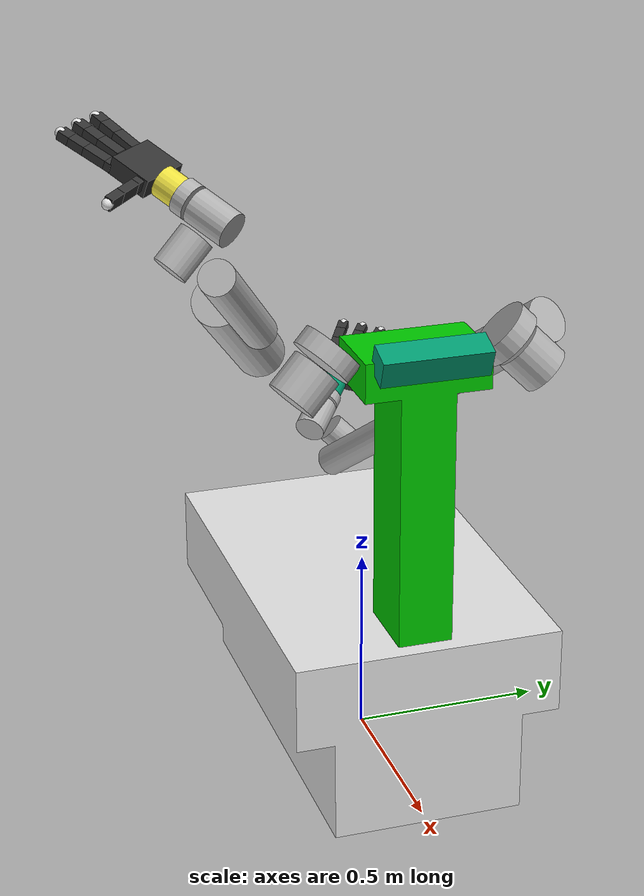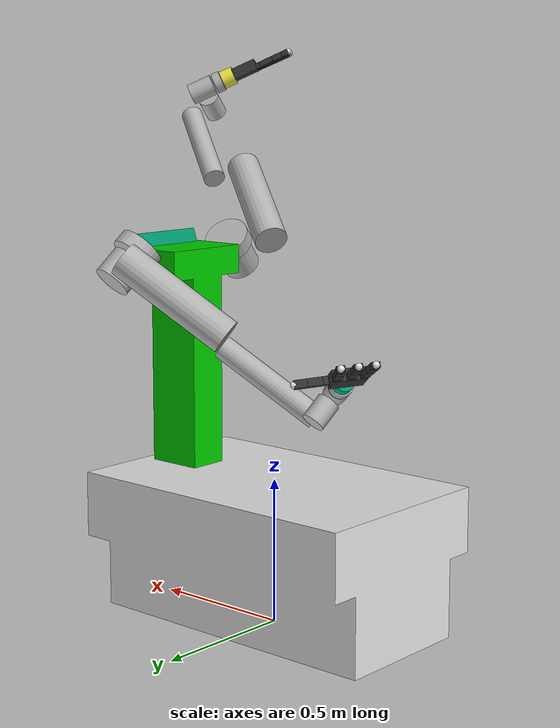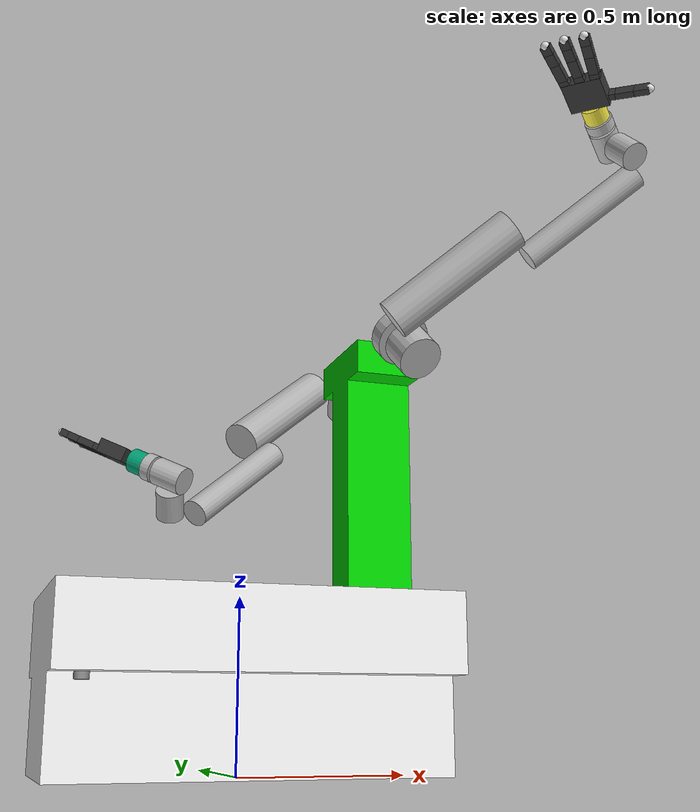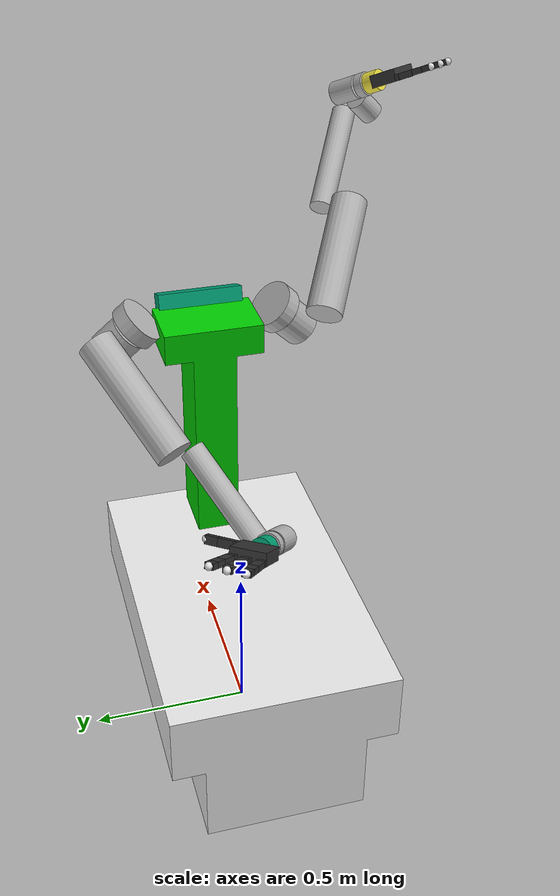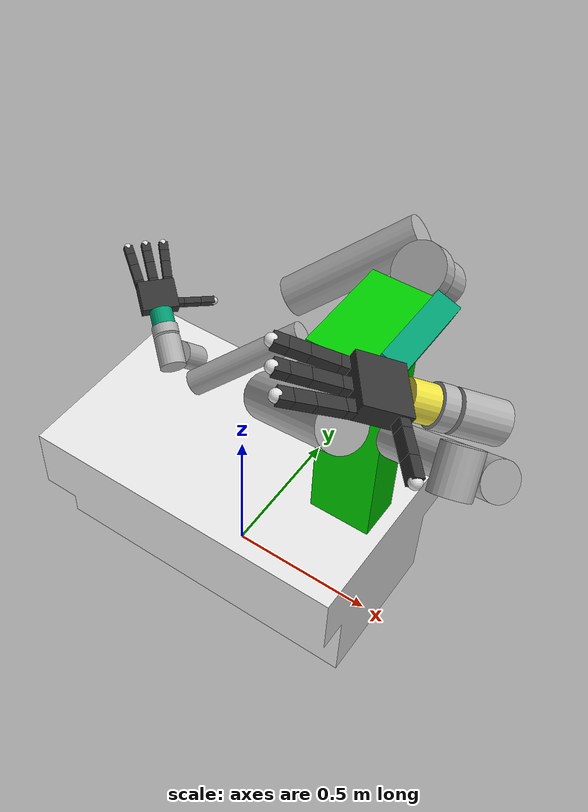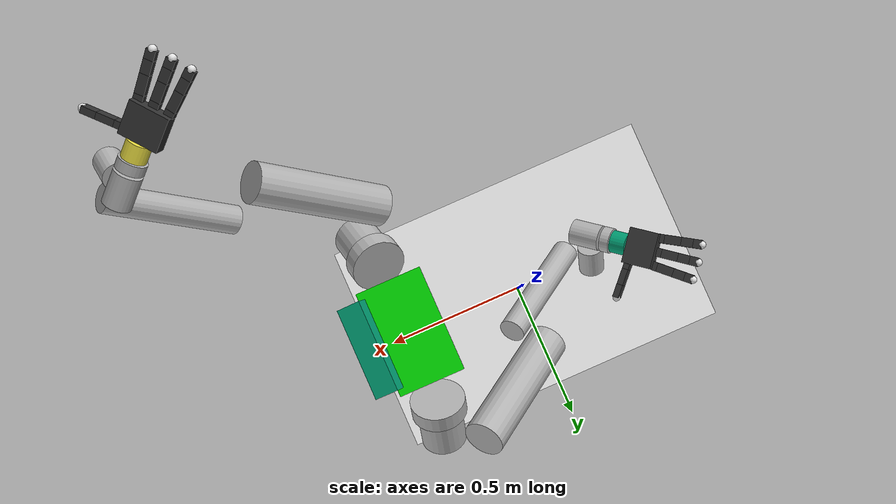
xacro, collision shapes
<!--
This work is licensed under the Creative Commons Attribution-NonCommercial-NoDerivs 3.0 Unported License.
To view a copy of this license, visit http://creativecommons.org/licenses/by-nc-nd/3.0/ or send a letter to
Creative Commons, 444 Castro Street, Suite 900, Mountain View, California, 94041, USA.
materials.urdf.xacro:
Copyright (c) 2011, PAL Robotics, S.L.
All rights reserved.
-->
<?xml version="1.0"?>
<robot name="tomm" xmlns:xacro="http://www.ros.org/wiki/xacro"
        xmlns:sensor="http://playerstage.sourceforge.net/gazebo/xmlschema/#sensor"
        xmlns:controller="http://playerstage.sourceforge.net/gazebo/xmlschema/#controller"
        xmlns:interface="http://playerstage.sourceforge.net/gazebo/xmlschema/#interface">

  <!-- Parameters -->
  <xacro:arg name="skin_version" default="full"/>

  <xacro:property name="skin_version" value="$(arg skin_version)" />
  <xacro:if value="${skin_version not in ['full','hands', 'left', 'right']}">
    <xacro:wrong_skin_version/>
  </xacro:if>

	<!--Common definitions -->
	<xacro:include filename="$(find tomm_description)/urdf/common.xacro"/>
  <xacro:include filename="$(find tomm_description)/urdf/materials.urdf.xacro"/>

	<!-- ROS_Control plugins -->
  <xacro:include filename="$(find tomm_description)/urdf/gazebo.urdf.xacro" />

	<!-- xacro macros Base -->
	<xacro:include filename="$(find tomm_description)/urdf/base/base.urdf.xacro"/>

	<!-- xacro macros Sensors -->
	<xacro:include filename="$(find tomm_description)/urdf/sensors/lidar.urdf.xacro"/>

  <!-- camera sensor -->
  <xacro:include filename="$(find tomm_description)/urdf/sensors/asus_xtiion_pro.urdf.xacro"/>

  <!-- xacro gazbeo plugin macros Sensors -->
  <xacro:include filename="$(find tomm_description)/urdf/sensors/lidar.gazebo.xacro" />
  <xacro:include filename="$(find tomm_description)/urdf/sensors/ftsensor.gazebo.xacro" />

	<!--xacro macros Arms-->
	<xacro:include filename="$(find tomm_description)/urdf/arm/arms.urdf.xacro"/>

  <!--xacro macros Hands-->
  <xacro:include filename="$(find tomm_description)/urdf/hand/hands.urdf.xacro"/>

	<!-- robot base, includes base, torso, wheels and logos -->
	<xacro:tom_base_v0 name="base" />

	<!-- robot head, includes the left camera -->
	<link name="tom_left_camera_link">
    <visual>
      <origin rpy="0 0 0" xyz="0 0 0"/>
      <geometry>
       <box size="0.01 0.01 0.01"/>
      </geometry>
      <material name="orange">
         <color rgba="0.45 0.45 0.45 1.0"/>
       </material>
    </visual>
  </link>

  <link name="tom_head_link">
    <visual>
      <origin rpy="1.57079632679 0 -1.57079632679" xyz="1 1.255 -0.838"/>
      <geometry>
        <mesh filename="package://tomm_description/meshes/head/head.stl" scale="0.001 0.001 0.001"/>
      </geometry>
      <material name="green">
         <color rgba="0.0 0.8 0.0 1"/>
       </material>
    </visual>
  </link>

  <joint name="table_head_joint" type="fixed">
		<origin rpy="0 0 0" xyz="0 0 0"/>
    <parent link="torso_link"/>
    <child link="tom_head_link"/>
  </joint>

  <joint name="tom_left_camera_joint" type="fixed">
    <origin rpy="-2.43606 -0.193804 -1.648299" xyz="0.075241 0.032279 0.211305"/>
    <parent link="torso_link"/>
    <child link="tom_left_camera_link"/>
  </joint>

	<!-- Arms -->
	<!-- Left Arm -->
	<xacro:tom_arm_v0 right_arm="false"/>
	<!-- Right Arm -->
	<xacro:tom_arm_v0 right_arm="true"/>

	<!-- Hands -->
	<!-- Left Hand -->
	<xacro:tom_hand_v0 right_hand="false"/>
  <!-- Right hand -->
	<xacro:tom_hand_v0 right_hand="true"/>

	<!-- sensors frames -->
	<xacro:tom_lidar_v0 name="laser" />

  <!-- sensor gazbeo plugins -->
  <xacro:tom_ft_gazebo name="right_wrist_ft" joint="r_wrist_3" ros_topic="tomm/right_wrist_ft" update_rate="200"/>
  <xacro:tom_ft_gazebo name="left_wrist_ft" joint="l_wrist_3" ros_topic="tomm/left_wrist_ft" update_rate="200"/>

  <xacro:tom_laser_gazebo prefix="tomm/" name="front_lidar" link="front_laser_scanner" ros_topic="tomm/front_scan" update_rate="50" min_angle="0.0" max_angle="3.141" nrays="180"/>
  <xacro:tom_laser_gazebo prefix="tomm/" name="rear_lidar" link="rear_laser_scanner" ros_topic="tomm/rear_scan" update_rate="50" min_angle="0.0" max_angle="3.141" nrays="180"/>

  <xacro:sensor_asus_xtion_pro name="tomm/asus" parent="torso_link">
      <origin xyz="0.11 0.0225 0.0" rpy="0 ${20*DEG2RAD} 0" />
  </xacro:sensor_asus_xtion_pro>

  <!-- skin sensing -->
  <xacro:if value="${skin_version == 'full'}">
    <xacro:include filename="$(find tomm_description)/urdf/skin/full_skin.urdf.xacro" />
  </xacro:if>
  <xacro:if value="${skin_version == 'hands'}">
    <xacro:include filename="$(find tomm_description)/urdf/skin/hands_skin.urdf.xacro" />
  </xacro:if>
  <xacro:if value="${skin_version == 'right'}">
    <xacro:include filename="$(find tomm_description)/urdf/skin/right_skin.urdf.xacro" />
  </xacro:if>
  <xacro:if value="${skin_version == 'left'}">
    <xacro:include filename="$(find tomm_description)/urdf/skin/left_skin.urdf.xacro" />
  </xacro:if>

</robot>

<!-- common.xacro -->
<robot name="tom" xmlns:xacro="http://www.ros.org/wiki/xacro">
  <xacro:property name="M_PI" value="3.1415926535897931" />
  <xacro:property name="VELOCITY_LIMIT_SCALE" value="0.6" />
  <xacro:property name="DEG2RAD" value="0.01745329251994329577" />

  <!--Base Parameters -->
  <xacro:property name="base_frame_mass" value="250.0" />

  <xacro:property name="base_hight" value="0.4" />
  <xacro:property name="base_width" value="0.60" />
  <xacro:property name="base_length" value="1.0" />
  <xacro:property name="base_collision_offset" value="0.10" />

  <xacro:property name="base_x_origin" value="0.4" />
  <xacro:property name="base_z_origin" value="0.5" />

  <!--Torso Parameters -->
  <xacro:property name="torso_hight" value="0.75" />
  <xacro:property name="torso_width" value="0.45" />
  <xacro:property name="torso_length" value="0.125" />
  <xacro:property name="torso_collision_offset" value="0.10" />

  <!--Wheel Parameters -->
  <xacro:property name="wheel_radius" value="0.1" />
  <xacro:property name="wheel_length" value="0.075" />

  <!--Sensor Parameters -->
  <xacro:property name="laser_hight" value="0.05" />
  <xacro:property name="laser_radius" value="0.02" />

  <!--Offset Parameters -->
  <xacro:property name="jr3_hight" value="0.05" />
  <xacro:property name="jr3_radius" value="0.035" />

  <xacro:property name="arm_joint_y_offset" value="0.225" />
  <xacro:property name="arm_joint_roll_offset" value="2.6061" />
  <xacro:property name="arm_joint_pitch_offset" value="0.6271" />

  <xacro:property name="adapter_z_offset" value="0.045" />
  <xacro:property name="adapter_joint_x_offset" value="0.045" />

  <xacro:property name="floor_to_base_frame" value="0.5" />

</robot>

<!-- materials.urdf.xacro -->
<robot name="tom">
  <material name="Blue">
    <color rgba="0.0 0.0 0.8 1.0"/>
  </material>

  <material name="Green">
    <color rgba="0.0 0.8 0.0 1.0"/>
  </material>

  <material name="Grey">
    <color rgba="0.7 0.7 0.7 1.0"/>
  </material>

  <material name="LightGrey">
    <color rgba="0.9 0.9 0.9 1.0"/>
  </material>

 <material name="DarkGrey">
   <color rgba="0.2 0.2 0.2 1.0"/>
 </material>

  <material name="Red">
    <color rgba="0.8 0.0 0.0 1.0"/>
  </material>

  <material name="White">
    <color rgba="1.0 1.0 1.0 1.0"/>
  </material>
</robot>

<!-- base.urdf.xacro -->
<robot xmlns:sensor="http://playerstage.sourceforge.net/gazebo/xmlschema/#sensor"
       xmlns:controller="http://playerstage.sourceforge.net/gazebo/xmlschema/#controller"
       xmlns:interface="http://playerstage.sourceforge.net/gazebo/xmlschema/#interface"
       xmlns:xacro="http://ros.org/wiki/xacro">

	<!--Common definitions -->
	<xacro:include filename="$(find tomm_description)/urdf/common.xacro"/>

	<!-- xacro macros Wheels-->
	<xacro:include filename="$(find tomm_description)/urdf/wheels/wheels.urdf.xacro"/>

	<!-- xacro base (includes: base, Logos, Torso, wheels) -->
	<xacro:macro name="tom_base_v0" params="name">

	<!-- Mobile base block  -->
	<link name="${name}_link">
	    <visual>
		    <origin xyz="${base_x_origin} 0 ${base_z_origin}" rpy="${90*DEG2RAD} 0 ${90*DEG2RAD}" />
		    <geometry>
		        <mesh filename="package://tomm_description/meshes/base/item_profile.dae"/>
		    </geometry>
		    <material name="LightGrey"/>
			</visual>
			<collision>
					<geometry>
		        	<mesh filename="package://tomm_description/meshes/base/item_profile_collision.dae" scale="0.001 0.0009 0.001"/>
					</geometry>
					<origin xyz="${base_x_origin + 0.15} ${(base_hight + base_collision_offset)/2 + 0.1} ${base_z_origin - 0.47 - 0.025}" rpy="${90*DEG2RAD} 0 ${-90*DEG2RAD}" />
           <surface>
                <friction>
                <ode>
                    <mu>0</mu>
                    <mu2>0</mu2>
                    <slip1>0</slip1>
                    <slip2>0</slip2>
                </ode>
                </friction>
            </surface>
			</collision>
			<inertial>
					<origin xyz="${base_x_origin - 0.45} 0 ${base_z_origin - 0.5}" />
					<mass value="${base_frame_mass}"/>
					<inertia ixx="340.82" ixy="0.001" ixz="0.001" iyy="380.20" iyz="0.001" izz="230.54"/>  <!-- inertias are set big to prevent base floating in gazebo -->
			</inertial>
	</link>

	<!-- Torso link -->
	<link name="torso_link">
	    <visual>
	        <origin xyz="-0.01614 0 -0.76268" rpy="1.57 0 1.57" />
	        <geometry>
	            <mesh filename="package://tomm_description/meshes/base/green_parts.dae"/>
	        </geometry>
	        <material name="Green"/>
	    </visual>
	    <collision>
	        <geometry>
                <mesh filename="package://tomm_description/meshes/base/green_parts_collision.dae"/>
	        </geometry>
		    <origin xyz="-0.11 -0.16 -0.8" rpy="${90*DEG2RAD} 0 ${90*DEG2RAD}" />
        </collision>

		<inertial>
		    <origin xyz="0 0 0.44" />
		    <mass value="25"/>
		    <inertia ixx="8.9" ixy="0.017" ixz="0.01" iyy="6.37" iyz="2.2" izz="6.33"/>
		</inertial>

	</link>

    <joint name="${name}_to_torso" type="fixed">
        <parent link="${name}_link"/>
        <child link="torso_link"/>
		<origin xyz="${base_x_origin + 0.01614} 0 ${base_z_origin + 0.76268}"/>
	</joint>

	<!-- Wheels-->

	<xacro:wheel parent="${name}_link" prefix="l_front_" reflect="1">
	    <origin xyz="${base_x_origin} 0.303 ${base_z_origin - 0.40}" rpy="-1.57 0 0" />
	</xacro:wheel>

	<xacro:wheel parent="${name}_link" prefix="l_rear_" reflect="1">
	    <origin xyz="${base_x_origin - 0.8115} 0.303 ${base_z_origin - 0.40}" rpy="-1.57 0 0" />
	</xacro:wheel>

	<xacro:wheel parent="${name}_link" prefix="r_front_" reflect="-1">
	    <origin xyz="${base_x_origin} -0.303 ${base_z_origin - 0.40}" rpy="-1.57 0 0" />
	</xacro:wheel>

	<xacro:wheel parent="${name}_link" prefix="r_rear_" reflect="-1">
	    <origin xyz="${base_x_origin - 0.8115} -0.303 ${base_z_origin - 0.40}" rpy="-1.57 0 0" />
	</xacro:wheel>

    <!-- Deco Logos-->

	  <link name="ICS_logo_blue_link">
		 <visual>
		  <origin xyz="0 0 0" rpy="1.57 0 1.57" />
		   <geometry>
		    <mesh filename="package://tomm_description/meshes/base/logo_blue.dae"/>
		   </geometry>
		 </visual>
		 <collision>
		  <origin xyz="0 0 0" rpy="1.57 0 1.57" />
		   <geometry>
		    <mesh filename="package://tomm_description/meshes/base/logo_blue.dae"/>
		   </geometry>
		 </collision>
		</link>

		<joint name="ICS_logo_blue" type="fixed">
		  <parent link="${name}_link"/>
		  <child link="ICS_logo_blue_link"/>
		  <origin xyz="${base_x_origin} 0 ${base_z_origin}"/>
		</joint>

		<link name="ICS_logo_grey_link">
		 <visual>
		  <origin xyz="0 0 0" rpy="1.57 0 1.57" />
		   <geometry>
		    <mesh filename="package://tomm_description/meshes/base/logo_grey.dae"/>
		   </geometry>
		 </visual>
		 <collision>
		  <origin xyz="0 0 0" rpy="1.57 0 1.57" />
		   <geometry>
		    <mesh filename="package://tomm_description/meshes/base/logo_grey.dae"/>
		   </geometry>
		 </collision>
		</link>

		<joint name="ICS_logo_grey" type="fixed">
		  <parent link="${name}_link"/>
		  <child link="ICS_logo_grey_link"/>
		  <origin xyz="${base_x_origin} 0 ${base_z_origin}"/>
		</joint>

		<!-- xacro macros gazebo-->
		<xacro:include filename="$(find tomm_description)/urdf/base/base.gazebo"/>

  </xacro:macro>
</robot>

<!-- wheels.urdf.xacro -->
<robot xmlns:xacro="http://www.ros.org/wiki/xacro" name="tom">

<xacro:include filename="$(find tomm_description)/urdf/wheels/wheels.transmission.xacro"/>

<xacro:macro name="cyl_inertia" params="mass r h">
    <inertial>
        <mass value="${mass}" />
        <inertia ixx="${(1/12)*mass*(3*r*r+h*h)}" ixy="0.0" ixz="0.0" iyy="${(1/12)*mass*(3*r*r+h*h)}" iyz="0.0" izz="${(1/2)*mass*r*r}" />
    </inertial>
</xacro:macro>

<xacro:macro name="wheel" params="parent prefix reflect *origin">
    <link name="${prefix}wheel_link">
        <visual>
            <geometry>
                <mesh filename="package://tomm_description/meshes/wheels/wheels.dae"/>
            </geometry>
            <material name="white">
                <color rgba="1 1 1 1"/>
            </material>
        </visual>
        <xacro:cyl_inertia mass="2.0" r="${wheel_radius}" h="${wheel_length}"/>
    </link>

    <gazebo reference="${prefix}wheel_link">
        <material>Gazebo/Grey</material>
    </gazebo>

    <!-- continuous not working! -->
    <joint name="${prefix}wheel_joint" type="fixed">
        <parent link="${parent}"/>
        <child link="${prefix}wheel_link" />
        <dynamics damping="0" friction="0"/>
        <xacro:insert_block name="origin" />
        <axis xyz="0 0 1" />
    </joint>

    <!--xacro:wheels_transmission prefix="${prefix}"/-->

</xacro:macro>

</robot>

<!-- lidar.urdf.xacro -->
<robot xmlns:sensor="http://playerstage.sourceforge.net/gazebo/xmlschema/#sensor"
       xmlns:controller="http://playerstage.sourceforge.net/gazebo/xmlschema/#controller"
       xmlns:interface="http://playerstage.sourceforge.net/gazebo/xmlschema/#interface"
       xmlns:xacro="http://ros.org/wiki/xacro">

	<!--Common definitions -->
	<xacro:include filename="$(find tomm_description)/urdf/common.xacro"/>

	<!-- xacro sensors  -->
	<xacro:macro name="tom_lidar_v0" params="name">

		<!-- Sensors -->
		<link name="front_${name}_scanner_link">
		 	<visual>
		  	<origin xyz="0 0 0" rpy="0 0 0" />
		   		<geometry>
		      	<cylinder length="${laser_hight}" radius="${laser_radius}" />
		   		</geometry>
		   		<material name="light_grey">
		     		<color rgba="0.5 0.5 0.5 1"/>
		   		</material>
		 	</visual>
			<collision>
		  	<origin xyz="0 0 0" rpy="0 0 0" />
		    <geometry>
		    	<cylinder length="${laser_hight}" radius="${laser_radius}" />
		    </geometry>
		  </collision>
		</link>

		<joint name="front_${name}_scanner" type="fixed">
		  <parent link="base_link"/>
		  <child link="front_${name}_scanner_link"/>
		  <origin xyz="${base_x_origin + 0.01464} 0.26511 ${base_z_origin - 0.22}" rpy="3.14 0 0.785"/>
		</joint>

		<link name="rear_${name}_scanner_link">
		 <visual>
		  <origin xyz="0 0 0" rpy="0 0 0" />
		   <geometry>
		     <cylinder length="${laser_hight}" radius="${laser_radius}" />
		   </geometry>
		   <material name="light_grey"/>
		 </visual>
			<collision>
		  	<origin xyz="0 0 0" rpy="0 0 0" />
		    <geometry>
		    	<cylinder length="${laser_hight}" radius="${laser_radius}" />
		    </geometry>
		  </collision>
		</link>

		<joint name="rear_${name}_scanner" type="fixed">
		  <parent link="base_link"/>
		  <child link="rear_${name}_scanner_link"/>
		  <origin xyz="${base_x_origin - 0.86614} -0.26415 ${base_z_origin - 0.22}" rpy="3.14 0 -2.355"/>
		</joint>

  </xacro:macro>

</robot>

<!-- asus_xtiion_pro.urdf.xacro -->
<robot name="sensor_asus_xtion_pro" xmlns:xacro="http://ros.org/wiki/xacro">

     <xacro:property name="asus_xtion_scale" value="0.001"/>
     <xacro:property name="asus_xtion_pro_depth_rel_rgb_py" value="0.0270" />
     <xacro:property name="asus_xtion_pro_rgb_rel_rgb_py"   value="-0.0220" />
     <xacro:property name="M_PI" value="3.1415926535897931" />

     <xacro:macro name="sensor_asus_xtion_pro" params="name parent *origin">

          <joint name="${name}_rgb_joint" type="fixed">
               <xacro:insert_block name="origin" />
               <parent link="${parent}"/>
               <child link="${name}_rgb_frame" />
          </joint>

          <link name="${name}_rgb_frame">
               <inertial>
                    <mass value="0.001" />
                    <origin xyz="0 0 0" />
                    <inertia ixx="0.0001" ixy="0.0" ixz="0.0" iyy="0.0001" iyz="0.0" izz="0.0001" />
               </inertial>
          </link>

          <joint name="${name}_rgb_optical_joint" type="fixed">
               <origin xyz="0 0 0" rpy="${-M_PI/2} 0 ${-M_PI/2}" />
               <parent link="${name}_rgb_frame" />
               <child link="${name}_rgb_optical_frame" />
          </joint>

          <link name="${name}_rgb_optical_frame">
               <inertial>
                    <mass value="0.001" />
                    <origin xyz="0 0 0" />
                    <inertia ixx="0.0001" ixy="0.0" ixz="0.0" iyy="0.0001" iyz="0.0" izz="0.0001" />
               </inertial>
          </link>

          <joint name="${name}_joint" type="fixed">
               <origin xyz="0 ${asus_xtion_pro_rgb_rel_rgb_py} 0" rpy="0 0 0"/>
               <parent link="${name}_rgb_frame"/>
               <child link="${name}_link"/>
          </joint>

          <link name="${name}_link">
               <visual>
                    <origin xyz="-0.01 0 0" rpy="${-M_PI/2} -${M_PI} ${-M_PI/2}"/>
                    <geometry>
                         <mesh filename="package://tomm_description/meshes/cameras/asus/asus_xtion_pro_live.dae" scale="${asus_xtion_scale} ${asus_xtion_scale} ${asus_xtion_scale}"/>
                    </geometry>
               </visual>
               <collision>
                    <origin xyz="0.0 0.0 0.0" rpy="0 0 0" />
                    <geometry>
                         <box size="0.0730 .2760 0.0720"/>
                    </geometry>
               </collision>
               <inertial>
                    <mass value="0.01" />
                    <origin xyz="0 0 0" />
                    <inertia ixx="0.001" ixy="0.0" ixz="0.0" iyy="0.001" iyz="0.0" izz="0.001" />
               </inertial>
          </link>

          <joint name="${name}_depth_joint" type="fixed">
               <origin xyz="0 ${asus_xtion_pro_depth_rel_rgb_py} 0" rpy="0 0 0" />
               <parent link="${name}_rgb_frame" />
               <child link="${name}_depth_frame" />
          </joint>

          <link name="${name}_depth_frame">
               <inertial>
                    <mass value="0.01" />
                    <origin xyz="0 0 0" />
                    <inertia ixx="0.001" ixy="0.0" ixz="0.0" iyy="0.001" iyz="0.0" izz="0.001" />
               </inertial>
          </link>

          <joint name="${name}_depth_optical_joint" type="fixed">
               <origin xyz="0 0 0" rpy="${-M_PI/2} 0 ${-M_PI/2}" />
               <parent link="${name}_depth_frame" />
               <child link="${name}_depth_optical_frame" />
          </joint>

          <link name="${name}_depth_optical_frame">
               <inertial>
                    <mass value="0.001" />
                    <origin xyz="0 0 0" />
                    <inertia ixx="0.0001" ixy="0.0" ixz="0.0" iyy="0.0001" iyz="0.0" izz="0.0001" />
               </inertial>
          </link>

          <!-- RGBD sensor for simulation, same as Kinect -->
          <sensor_xtion_pro_gazebo/>

     </xacro:macro>

     <!-- ====================================================
                           Gazebo
     ========================================================= -->

     <xacro:macro name="sensor_xtion_pro_gazebo">
          <gazebo reference="${name}_depth_frame">
               <sensor type="depth" name="${name}_sensor">
                    <always_on>true</always_on>
                    <update_rate>10.0</update_rate>
                    <camera>
                         <horizontal_fov>${60.0*M_PI/180.0}</horizontal_fov>
                         <image>
                              <format>R8G8B8</format>
                              <width>640</width>
                              <height>480</height>
                         </image>
                         <clip>
                              <near>0.05</near>
                              <far>10</far>
                         </clip>
                    </camera>

                    <plugin name="${name}_controller" filename="libgazebo_ros_openni_kinect.so">
                         <cameraName>${name}</cameraName>
                         <alwaysOn>true</alwaysOn>
                         <updateRate>10</updateRate>
                         <imageTopicName>rgb/image_raw</imageTopicName>
                         <depthImageTopicName>depth/image_raw</depthImageTopicName>
                         <pointCloudTopicName>depth/points</pointCloudTopicName>
                         <cameraInfoTopicName>rgb/camera_info</cameraInfoTopicName>
                         <depthImageCameraInfoTopicName>depth/camera_info</depthImageCameraInfoTopicName>
                         <frameName>${name}_depth_optical_frame</frameName>
                         <baseline>0.1</baseline>
                         <distortion_k1>0.0</distortion_k1>
                         <distortion_k2>0.0</distortion_k2>
                         <distortion_k3>0.0</distortion_k3>
                         <distortion_t1>0.0</distortion_t1>
                         <distortion_t2>0.0</distortion_t2>
                         <pointCloudCutoff>0.4</pointCloudCutoff>
                    </plugin>
               </sensor>
          </gazebo>
     </xacro:macro>
</robot>

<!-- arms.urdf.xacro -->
<robot xmlns:sensor="http://playerstage.sourceforge.net/gazebo/xmlschema/#sensor"
       xmlns:controller="http://playerstage.sourceforge.net/gazebo/xmlschema/#controller"
       xmlns:interface="http://playerstage.sourceforge.net/gazebo/xmlschema/#interface"
       xmlns:xacro="http://ros.org/wiki/xacro">

	<!--Common definitions -->
	<xacro:include filename="$(find tomm_description)/urdf/common.xacro"/>

	<!-- Hand specializations -->
	<!--xacro macros Arms-->
	<xacro:include filename="$(find tomm_description)/urdf/arm/ur5/ur5.urdf.xacro"/>

	<!-- xacro arms (right_arm=true -> right arm, false -> left arm -->
	<xacro:macro name="tom_arm_v0" params="right_arm">

		<xacro:unless value="${right_arm}">
			<!-- left UR5 robot model -->
			<xacro:ur5_robot prefix="l_" joint_limited="false"/>
			<joint name="torso_to_l_arm" type="fixed">
				<parent link="torso_link"/>
				<child link="l_base_link"/>
				<origin xyz="0 ${arm_joint_y_offset} 0" rpy="${arm_joint_roll_offset} ${arm_joint_pitch_offset} -2.6061"/>
			</joint>

			<!-- This is the JR3 adapter -->
			<link name="l_hand_base_adapter_link">
			    <visual>
				    <origin xyz="0 0 -${adapter_z_offset}" rpy="${M_PI/2} 0 ${M_PI/2}" />
				    <geometry>
				        <mesh filename="package://tomm_description/meshes/arm/hand_mount.dae"/>
				    </geometry>
			    </visual>
			    <collision>
					<origin xyz="0 0 ${-jr3_hight/2}" rpy="0 0 0" />
				    <geometry>
				  	    <cylinder length="${jr3_hight}" radius="${jr3_radius}" />
				    </geometry>
				</collision>
			</link>

			<joint name="l_hand_base_adapter_joint" type="fixed">
				<parent link="l_ee_link"/>
				<child link="l_hand_base_adapter_link"/>
				<origin xyz="${adapter_joint_x_offset} 0 0" rpy="${M_PI/2} 0.785 ${M_PI/2}"/>
			</joint>

		</xacro:unless>

		<xacro:if value="${right_arm}">
			<!-- right UR5 robot model -->
			<xacro:ur5_robot prefix="r_" joint_limited="false"/>
			<joint name="torso_to_r_arm" type="fixed">
				<parent link="torso_link"/>
				<child link="r_base_link"/>
				<origin xyz="0 -${arm_joint_y_offset} 0" rpy="${arm_joint_roll_offset} -${arm_joint_pitch_offset} -0.5355"/>
			</joint>

			<!-- This is the JR3 adapter -->
			 <link name="r_hand_base_adapter_link">
			 <visual>
				<origin xyz="0 0 -${adapter_z_offset}" rpy="${M_PI/2} 0 ${M_PI/2}" />
				 <geometry>
				  <mesh filename="package://tomm_description/meshes/arm/hand_mount.dae"/>
				 </geometry>
			 </visual>
			 <collision>
					<origin xyz="0 0 ${-jr3_hight/2}" rpy="0 0 0" />
				  <geometry>
				  	<cylinder length="${jr3_hight}" radius="${jr3_radius}" />
				  </geometry>
				</collision>
			</link>
			<joint name="r_hand_base_adapter_joint" type="fixed">
				<parent link="r_ee_link"/>
				<child link="r_hand_base_adapter_link"/>
				<origin xyz="${adapter_joint_x_offset} 0 0" rpy="${M_PI/2} 2.356 ${M_PI/2}"/>
			</joint>

		</xacro:if>

  </xacro:macro>

</robot>

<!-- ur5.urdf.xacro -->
<robot xmlns:xacro="http://www.ros.org/wiki/xacro">

  <xacro:include filename="$(find tomm_description)/urdf/arm/ur5/ur5.transmission.xacro"/>
  <xacro:include filename="$(find tomm_description)/urdf/arm/ur5/ur5.gazebo"/>

  <xacro:property name="pi" value="3.14159265" />

  <!-- Inertia parameters -->
  <xacro:property name="base_mass" value="4.0" />  <!-- This mass might be incorrect -->
  <xacro:property name="shoulder_mass" value="3.7000" />
  <xacro:property name="upper_arm_mass" value="8.3930" />
  <xacro:property name="forearm_mass" value="2.2750" />
  <xacro:property name="wrist_1_mass" value="1.2190" />
  <xacro:property name="wrist_2_mass" value="1.2190" />
  <xacro:property name="wrist_3_mass" value="0.1879" />

  <xacro:property name="shoulder_cog" value="0.0 0.00193 -0.02561" />
  <xacro:property name="upper_arm_cog" value="0.0 -0.024201 0.2125" />
  <xacro:property name="forearm_cog" value="0.0 0.0265 0.11993" />
  <xacro:property name="wrist_1_cog" value="0.0 0.110949 0.01634" />
  <xacro:property name="wrist_2_cog" value="0.0 0.0018 0.11099" />
  <xacro:property name="wrist_3_cog" value="0.0 0.001159 0.0" />

  <!-- Kinematic model -->
  <!-- Properties from urcontrol.conf -->
  <xacro:property name="ur5_d1" value="0.089159" />
  <xacro:property name="ur5_a2" value="0.42500" />
  <xacro:property name="ur5_a3" value="0.39225" />
  <xacro:property name="ur5_d4" value="0.10915" />
  <xacro:property name="ur5_d5" value="0.09465" />
  <xacro:property name="ur5_d6" value="0.0823" />

  <!-- Arbitrary offsets for shoulder/elbow joints -->
  <xacro:property name="shoulder_offset" value="0.13585" />  <!-- measured from model -->
  <xacro:property name="elbow_offset" value="-0.1197" /> <!-- measured from model -->

  <!-- link lengths used in model -->
  <xacro:property name="shoulder_height" value="${ur5_d1}" />
  <xacro:property name="upper_arm_length" value="${ur5_a2}" />
  <xacro:property name="forearm_length" value="${ur5_a3}" />
  <xacro:property name="wrist_1_length" value="${ur5_d4 - elbow_offset - shoulder_offset}" />
  <xacro:property name="wrist_2_length" value="${ur5_d5}" />
  <xacro:property name="wrist_3_length" value="${ur5_d6}" />
  <!--xacro:property name="shoulder_height" value="0.089159" /-->
  <!--xacro:property name="shoulder_offset" value="0.13585" /-->  <!-- shoulder_offset - elbow_offset + wrist_1_length = 0.10915 -->
  <!--xacro:property name="upper_arm_length" value="0.42500" /-->
  <!--xacro:property name="elbow_offset" value="0.1197" /-->       <!-- CAD measured -->
  <!--xacro:property name="forearm_length" value="0.39225" /-->
  <!--xacro:property name="wrist_1_length" value="0.093" /-->     <!-- CAD measured -->
  <!--xacro:property name="wrist_2_length" value="0.09465" /-->   <!-- In CAD this distance is 0.930, but in the spec it is 0.09465 -->
  <!--xacro:property name="wrist_3_length" value="0.0823" /-->

  <xacro:property name="shoulder_radius" value="0.060" />   <!-- manually measured -->
  <xacro:property name="upper_arm_radius" value="0.054" />  <!-- manually measured -->
  <xacro:property name="elbow_radius" value="0.060" />      <!-- manually measured -->
  <xacro:property name="forearm_radius" value="0.040" />    <!-- manually measured -->
  <xacro:property name="wrist_radius" value="0.045" />      <!-- manually measured -->

    <xacro:macro name="cylinder_inertial" params="radius length mass *origin">
        <mass value="${mass}" />
        <xacro:insert_block name="origin" />
        <inertia ixx="${0.0833333 * mass * (3 * radius * radius + length * length)}" ixy="0.0" ixz="0.0"
                 iyy="${0.0833333 * mass * (3 * radius * radius + length * length)}" iyz="0.0"
                 izz="${0.5 * mass * radius * radius}" />
    </xacro:macro>

    <xacro:macro name="ur5_robot" params="prefix joint_limited">

        <link name="${prefix}base_link" >

            <visual>
                <geometry>
                    <mesh filename="package://tomm_description/meshes/arm/ur5/visual/Base.dae" />
                </geometry>
                <material name="LightGrey">
                    <color rgba="0.7 0.7 0.7 1.0"/>
                </material>
            </visual>

            <collision>
                <geometry>
                    <!--mesh filename="package://tomm_description/meshes/arm/ur5/collision/base.stl" /-->
                    <cylinder length="0.05" radius="0.08"/>
                </geometry>
            </collision>

            <inertial>
                <xacro:cylinder_inertial radius="0.06" length="0.05" mass="${base_mass}">
                    <origin xyz="0.0 0.0 0.0" rpy="0 0 0" />
                </xacro:cylinder_inertial>
            </inertial>
        </link>

        <joint name="${prefix}shoulder_pan_joint" type="revolute">
            <parent link="${prefix}base_link" />
            <child link = "${prefix}shoulder_link" />
            <origin xyz="0.0 0.0 ${shoulder_height}" rpy="0.0 0.0 0.0" />
            <axis xyz="0 0 1" />
            <xacro:unless value="${joint_limited}">
                <limit lower="${-pi}" upper="${pi}" effort="500.0" velocity="3.15"/>
            </xacro:unless>
            <xacro:if value="${joint_limited}">
                <limit lower="${-pi}" upper="${pi}" effort="500.0" velocity="3.15"/>
            </xacro:if>
            <dynamics damping="1.0" friction="0.0"/>
        </joint>

        <link name="${prefix}shoulder_link">

            <visual>
                <geometry>
                    <mesh filename="package://tomm_description/meshes/arm/ur5/visual/Shoulder.dae" />
                </geometry>
                <material name="LightGrey">
                    <color rgba="0.7 0.7 0.7 1.0"/>
                </material>
            </visual>

            <collision>
                <geometry>
                    <!--mesh filename="package://tomm_description/meshes/arm/ur5/collision/shoulder.stl" /-->
                    <cylinder length="0.1" radius="0.065"/>
                </geometry>
            </collision>

            <inertial>
                <xacro:cylinder_inertial radius="0.06" length="0.15" mass="${shoulder_mass}">
                    <origin xyz="0.0 0.0 0.0" rpy="0 0 0" />
                </xacro:cylinder_inertial>
            </inertial>
        </link>

        <joint name="${prefix}shoulder_lift_joint" type="revolute">
            <parent link="${prefix}shoulder_link" />
            <child link = "${prefix}upper_arm_link" />
            <origin xyz="0.0 ${shoulder_offset} 0.0" rpy="0.0 ${pi / 2.0} 0.0" />
            <axis xyz="0 1 0" />
            <xacro:unless value="${joint_limited}">
                <limit lower="${-pi}" upper="${pi}" effort="500.0" velocity="3.15"/>
            </xacro:unless>
            <xacro:if value="${joint_limited}">
                <limit lower="${-pi}" upper="${pi}" effort="500.0" velocity="3.15"/>
            </xacro:if>
            <dynamics damping="1.0" friction="0.0"/>
        </joint>

        <link name="${prefix}upper_arm_link">

            <visual>
                <geometry>
                    <mesh filename="package://tomm_description/meshes/arm/ur5/visual/UpperArm.dae" />
                </geometry>
                <material name="LightGrey">
                    <color rgba="0.7 0.7 0.7 1.0"/>
                </material>
            </visual>

            <collision>
                <geometry>
                    <!--mesh filename="package://tomm_description/meshes/arm/ur5/collision/upper_arm.stl" /-->
                    <cylinder length="${ur5_a2}" radius="0.06"/> <!-- simon: reduced ${ur5_a2 - 0.11} -->
                </geometry>
                <origin xyz="0.0 0.0 ${ur5_a2/2}" rpy="0.0 0.0 0.0" />
            </collision>

            <inertial>
                <xacro:cylinder_inertial radius="0.06" length="0.56" mass="${upper_arm_mass}">
                    <origin xyz="0.0 0.0 0.28" rpy="0 0 0" />
                </xacro:cylinder_inertial>
            </inertial>
        </link>

        <joint name="${prefix}elbow_joint" type="revolute">
            <parent link="${prefix}upper_arm_link" />
            <child link = "${prefix}forearm_link" />
            <origin xyz="0.0 ${elbow_offset} ${upper_arm_length}" rpy="0.0 0.0 0.0" />
            <axis xyz="0 1 0" />
            <xacro:unless value="${joint_limited}">
                <limit lower="${-pi}" upper="${pi}" effort="500.0" velocity="3.15"/>
            </xacro:unless>
            <xacro:if value="${joint_limited}">
                <limit lower="${-pi}" upper="${pi}" effort="500.0" velocity="3.15"/>
            </xacro:if>
            <dynamics damping="1.0" friction="0.0"/>
        </joint>

        <link name="${prefix}forearm_link">

            <visual>
                <geometry>
                    <mesh filename="package://tomm_description/meshes/arm/ur5/visual/Forearm.dae" />
                </geometry>
                <material name="LightGrey">
                    <color rgba="0.7 0.7 0.7 1.0"/>
                </material>
            </visual>

            <collision>
                <geometry>
                    <!--mesh filename="package://tomm_description/meshes/arm/ur5/collision/forearm.stl" /-->
                    <cylinder length="${ur5_a3}" radius="${forearm_radius}"/>
                </geometry>
                <origin xyz="0.0 0.0 ${ur5_a3/2}" rpy="0.0 0.0 0.0" />
            </collision>
            <inertial>
                <xacro:cylinder_inertial radius="0.06" length="0.5" mass="${forearm_mass}">
                <origin xyz="0.0 0.0 0.25" rpy="0 0 0" />
                </xacro:cylinder_inertial>
            </inertial>
        </link>

        <joint name="${prefix}wrist_1_joint" type="revolute">
            <parent link="${prefix}forearm_link" />
            <child link = "${prefix}wrist_1_link" />
            <origin xyz="0.0 0.0 ${forearm_length}" rpy="0.0 ${pi / 2.0} 0.0" />
            <axis xyz="0 1 0" />
            <xacro:unless value="${joint_limited}">
                <limit lower="${-pi}" upper="${pi}" effort="500.0" velocity="3.2"/>
            </xacro:unless>
            <xacro:if value="${joint_limited}">
                <limit lower="${-pi}" upper="${pi}" effort="500.0" velocity="3.2"/>
            </xacro:if>
            <dynamics damping="1.0" friction="0.0"/>
        </joint>

        <link name="${prefix}wrist_1_link">

            <visual>
                <geometry>
                    <mesh filename="package://tomm_description/meshes/arm/ur5/visual/Wrist1.dae" />
                </geometry>
                <material name="LightGrey">
                    <color rgba="0.7 0.7 0.7 1.0"/>
                </material>
            </visual>

            <collision>
                <geometry>
                    <!--mesh filename="package://tomm_description/meshes/arm/ur5/collision/wrist_1.stl" /-->
                    <cylinder length="${ur5_d4 - 0.02}" radius="${0.04}"/>
                </geometry>
                <origin xyz="0.0 ${ur5_d4 - 0.02} 0.0" rpy="0.0 0.0 0.0" />
            </collision>

            <inertial>
                <xacro:cylinder_inertial radius="0.6" length="0.12" mass="${wrist_1_mass}">
                    <origin xyz="0.0 0.0 0.0" rpy="${pi} 0 0" />
                </xacro:cylinder_inertial>
            </inertial>
        </link>

        <joint name="${prefix}wrist_2_joint" type="revolute">
            <parent link="${prefix}wrist_1_link" />
            <child link = "${prefix}wrist_2_link" />
            <origin xyz="0.0 ${wrist_1_length} 0.0" rpy="0.0 0.0 0.0" />
            <axis xyz="0 0 1" />
            <xacro:unless value="${joint_limited}">
                <limit lower="${-pi}" upper="${pi}" effort="500.0" velocity="3.2"/>
            </xacro:unless>
            <xacro:if value="${joint_limited}">
                <limit lower="${-pi}" upper="${pi}" effort="500.0" velocity="3.2"/>
            </xacro:if>
            <dynamics damping="1.0" friction="0.0"/>
        </joint>

        <link name="${prefix}wrist_2_link">

            <visual>
                <geometry>
                    <mesh filename="package://tomm_description/meshes/arm/ur5/visual/Wrist2.dae" />
                </geometry>
                <material name="LightGrey">
                    <color rgba="0.7 0.7 0.7 1.0"/>
                </material>
            </visual>

            <collision>
                <geometry>
                    <!--mesh filename="package://tomm_description/meshes/arm/ur5/collision/wrist_2.stl" /-->
                    <cylinder length="${ur5_d5 }" radius="${0.04}"/>
                </geometry>
                <origin xyz="0.0 -0.01 ${ur5_d5}" rpy="${pi/2.0} 0.0 0.0" />
            </collision>

            <inertial>
                <xacro:cylinder_inertial radius="0.6" length="0.12" mass="${wrist_2_mass}">
                    <origin xyz="0.0 0.0 0.0" rpy="0 0 0" />
                </xacro:cylinder_inertial>
            </inertial>
        </link>

        <joint name="${prefix}wrist_3_joint" type="revolute">
            <parent link="${prefix}wrist_2_link" />
            <child link = "${prefix}wrist_3_link" />
            <origin xyz="0.0 0.0 ${wrist_2_length}" rpy="0.0 0.0 0.0" />
            <axis xyz="0 1 0" />
            <xacro:unless value="${joint_limited}">
                <limit lower="${-pi}" upper="${pi}" effort="500.0" velocity="3.2"/>
            </xacro:unless>
            <xacro:if value="${joint_limited}">
                <limit lower="${-pi}" upper="${pi}" effort="500.0" velocity="3.2"/>
            </xacro:if>
            <dynamics damping="1.0" friction="0.0"/>
        </joint>

        <link name="${prefix}wrist_3_link">

            <visual>
                <geometry>
                    <mesh filename="package://tomm_description/meshes/arm/ur5/visual/Wrist3.dae" />
                </geometry>
                <material name="LightGrey">
                    <color rgba="0.7 0.7 0.7 1.0"/>
                </material>
            </visual>

            <collision>
                <geometry>
                    <!--mesh filename="package://tomm_description/meshes/arm/ur5/collision/wrist_3.stl" /-->
                    <cylinder length="0.03" radius="${0.04}"/>
                </geometry>
                <origin xyz="0 0.06 0" rpy="${pi/2.0} 0 0" />
            </collision>

            <inertial>
                <xacro:cylinder_inertial radius="0.6" length="0.12" mass="${wrist_3_mass}">
                    <origin xyz="0.0 0.0 0.0" rpy="0 0 0" />
                </xacro:cylinder_inertial>
            </inertial>
        </link>

        <joint name="${prefix}ee_fixed_joint" type="fixed">
            <parent link="${prefix}wrist_3_link" />
            <child link = "${prefix}ee_link" />
            <origin xyz="0.0 ${wrist_3_length} 0.0" rpy="0.0 0.0 ${pi/2.0}" />
        </joint>

        <link name="${prefix}ee_link">
            <collision>
                <geometry>
                    <box size="0.01 0.01 0.01"/>
                </geometry>
                <origin rpy="0 0 0" xyz="-0.01 0 0"/>
            </collision>
        </link>

  <xacro:ur5_arm_transmission prefix="${prefix}" />
  <xacro:ur5_arm_gazebo prefix="${prefix}"/>

  </xacro:macro>

</robot>

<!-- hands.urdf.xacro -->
<robot xmlns:sensor="http://playerstage.sourceforge.net/gazebo/xmlschema/#sensor"
       xmlns:controller="http://playerstage.sourceforge.net/gazebo/xmlschema/#controller"
       xmlns:interface="http://playerstage.sourceforge.net/gazebo/xmlschema/#interface"
       xmlns:xacro="http://ros.org/wiki/xacro">

	<!--Common definitions -->
	<xacro:include filename="$(find tomm_description)/urdf/common.xacro"/>

	<!-- Hand specializations -->
	<xacro:include filename="$(find tomm_description)/urdf/hand/allegro_hand/allegro_hand_right.urdf.xacro"/>
  <xacro:include filename="$(find tomm_description)/urdf/hand/allegro_hand/allegro_hand_left.urdf.xacro"/>

	<!-- xacro hands (right_hand=true -> right hand, false -> left hand -->
	<xacro:macro name="tom_hand_v0" params="right_hand">

		<xacro:unless value="${right_hand}">
			<xacro:allegro_hand_left prefix="l_hand_"/>
			<joint name="l_hand_base_joint" type="fixed">
		  	<parent link="l_hand_base_adapter_link"/>
		  	<child link="l_hand_base_link"/>
		  	<origin xyz="0.01 0 0.095" rpy="0 0 0"/>
  		</joint>
		</xacro:unless>
		<xacro:if value="${right_hand}">
			<xacro:allegro_hand_right prefix="r_hand_"/>
			<joint name="r_hand_base_joint" type="fixed">
		  	<parent link="r_hand_base_adapter_link"/>
		  	<child link="r_hand_base_link"/>
		  	<origin xyz="0.01 0 0.095" rpy="0 0 0"/>
  		</joint>
		</xacro:if>

  </xacro:macro>

</robot>

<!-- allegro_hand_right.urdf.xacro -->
<robot xmlns:xacro="http://www.ros.org/wiki/xacro">

<xacro:include filename="$(find tomm_description)/urdf/hand/allegro_hand/hands.transmission.xacro"/>
<xacro:include filename="$(find tomm_description)/urdf/hand/allegro_hand/hands.gazebo.xacro"/>

<xacro:property name="DEG2RAD" value="0.01745329251" />

<!-- ======================== BASE PARAMS ========================= -->

<xacro:property name="base_link_z" value="0.095" />

<!-- ======================== FINGER PARAMS ======================== -->

<xacro:property name="links_x" value="0.0196" />
<xacro:property name="links_y" value="0.0275" />

<xacro:property name="link0_z" value="0.0164" />
<xacro:property name="link1_z" value="0.0540" />
<xacro:property name="link2_z" value="0.0384" />

<!-- full height from joint to tip. when used,
the radius of the finger tip sphere will be subtracted
and one fixed link will be added for the tip. -->
<xacro:property name="link3_z" value="0.0387" />
<xacro:property name="fingerTip_r" value="0.0120" />

<xacro:property name="offset_origin_x_const" value="0" />
<xacro:property name="offset_origin_y_const" value="0.0435" />
<xacro:property name="offset_origin_z_const" value="-0.001542" />
<xacro:property name="offset_origin_z_mid_const" value="0.0007" />

<!-- ========================= THUMB PARAMS ========================= -->

<xacro:property name="link0_t_x" value="0.0358" />
<xacro:property name="link0_t_y" value="0.0340" />
<xacro:property name="link0_t_z" value="0.0455" />

<xacro:property name="link1_t_z" value="0.0177" />
<xacro:property name="link2_t_z" value="0.0514" />
<xacro:property name="link3_t_z" value="0.0543" />

<!-- ========================= LIMITS ========================= -->

<xacro:property name="joint_safety_margin" value="0.1" />
<xacro:property name="limit_0_up" value="0.57" />
<xacro:property name="limit_0_low" value="-0.57" />
<xacro:property name="limit_1_up" value="1.71" />
<xacro:property name="limit_1_low" value="-0.296" />
<xacro:property name="limit_2_up" value="1.809" />
<xacro:property name="limit_2_low" value="-0.274" />
<xacro:property name="limit_3_up" value="1.718" />
<xacro:property name="limit_3_low" value=" -0.327" />

<xacro:property name="limit_0_t_up" value="1.496" />
<xacro:property name="limit_0_t_low" value="0.363" />
<xacro:property name="limit_1_t_up" value="1.263" />
<xacro:property name="limit_1_t_low" value="-0.205" />
<xacro:property name="limit_2_t_up" value="1.744" />
<xacro:property name="limit_2_t_low" value="-0.289" />
<xacro:property name="limit_3_t_up" value="1.819" />
<xacro:property name="limit_3_t_low" value="-0.262" />

<!-- =============== Macro ================= -->
<xacro:macro name="allegro_hand_right" params="prefix">

  <!-- BASE -->
<link name="${prefix}base_link">

  	<visual>
    		<geometry>
      			<mesh filename="package://tomm_description/meshes/hand/base_link.STL" />
    		</geometry>

		<origin rpy="0 0 0" xyz="0 0 0 "/> -->

		<material name="black">
        		<color rgba="0.2 0.2 0.2 1"/>
      		</material>
	</visual>

    	<collision>
	    	<origin rpy="0 0 0" xyz="-0.009300 0 -${base_link_z/2}"/>
    		<geometry>
        		<box size="0.0408 0.1130 ${base_link_z}"/>
      		</geometry>
    	</collision>

		<inertial>
          <origin xyz="0 0 ${base_link_z/2}" rpy="0 0 0"/>
          <mass value="0.4154"/>
          <inertia
              ixx="1e-4" ixy="0.0" ixz="0.0"
              iyy="1e-4" iyz="0.0"
              izz="1e-4"/>
        </inertial>

</link>

<!-- FINGERS -->

<!-- RIGHT HAND due to which finger is number 0 -->
<!-- for LEFT HAND switch the sign of the **offset_origin_y** and **finger_angle_r** parameters-->
<xacro:finger
	prefix= 		"${prefix}"
	finger_num=			"0"
  finger_label=			"index"
	offset_origin_x=	"${offset_origin_x_const}"
	offset_origin_y=	"${offset_origin_y_const}"
	offset_origin_z=	"${offset_origin_z_const}"
	finger_angle_r=		"-${5.0*DEG2RAD}"
/>

<xacro:finger
	prefix= 		"${prefix}"
	finger_num=			"1"
  finger_label=			"middle"
	offset_origin_x=	"${offset_origin_x_const}"
	offset_origin_y=	"0"
	offset_origin_z=	"${offset_origin_z_mid_const}"
	finger_angle_r=		"0.0"
/>

<xacro:finger
	prefix= 		"${prefix}"
	finger_num=			"2"
  finger_label=			"ring"
	offset_origin_x=	"${offset_origin_x_const}"
	offset_origin_y=	"-${offset_origin_y_const}"
	offset_origin_z=	"${offset_origin_z_const}"
	finger_angle_r=		"${5.0*DEG2RAD}"
/>

<!-- THUMB -->

<xacro:thumb_right
	prefix= 		"${prefix}"
	finger_num=			"3"
  finger_label=     "thumb"
	offset_origin_x=	"-0.0182"
	offset_origin_y=	"0.019333"
	offset_origin_z=	"-0.045987"

	finger_angle_r=		"0"
	finger_angle_p=		"-${95*DEG2RAD}"
	finger_angle_y=		"-${90*DEG2RAD}"
/>

</xacro:macro>

<!-- THUMB MACRO -->
<xacro:macro name="thumb_right" params="prefix finger_num finger_label offset_origin_x offset_origin_y offset_origin_z finger_angle_r finger_angle_p finger_angle_y">

<!-- [LINK 12] -->
	<link name="${prefix}link_${finger_label}_0">

    	<visual>
			<geometry>
        		<!-- RIGHT -->
      			<mesh filename="package://tomm_description/meshes/hand/link_12.0_right.STL" />
      			<!-- LEFT -->
      		</geometry>
      		<material name="black">
        		<color rgba=".2 .2 .2 1"/>
      		</material>
    	</visual>

    	<collision>
      		<geometry>
        		<box size="${link0_t_x} ${link0_t_y} ${link0_t_z}"/>
      		</geometry>

  			<!-- RIGHT -->
            <origin rpy="0 0 0" xyz="${-0.0358/2+0.0} ${.018/2} ${.029/2}"/>
     		<!-- LEFT -->
    	</collision>

		<inertial>
              <mass value="0.0176" />
              <origin xyz="0 0 0" rpy="0 0 0"/>
              <inertia ixx="1.89273333333e-5" ixy="7.16716e-06" ixz="5.35568e-06"
                       iyy="1.43008213333e-05" iyz="6.8068e-06"
                       izz="1.89273333333e-05" />
		</inertial>
	</link>

	<joint name="${prefix}joint_${finger_label}_0" type="fixed">

    	<axis xyz="-1 0 0"/>
    	<limit effort="0" velocity="0" lower="${limit_0_t_low-joint_safety_margin}" upper="${limit_0_t_up-joint_safety_margin}" />
    	<parent link="${prefix}base_link"/>
    	<child link="${prefix}link_${finger_label}_0"/>
    	<origin rpy="${finger_angle_r} ${finger_angle_p} ${finger_angle_y}" xyz="${offset_origin_x} ${offset_origin_y} ${offset_origin_z}"/>
		<dynamics damping="1" friction="0"/>

	</joint>

<!-- [LINK 13] -->
	<link name="${prefix}link_${finger_label}_1">
		<visual>
			<geometry>
		    	<mesh filename="package://tomm_description/meshes/hand/link_13.0.STL" />
		  	</geometry>

		  	<material name="black">
		  		<color rgba=".2 .2 .2 1"/>
		 	</material>
		</visual>

		<collision>
			<geometry>
		    	<box size="${links_x} ${links_y} ${link1_t_z}"/>
		  	</geometry>

		  	<origin rpy="0 0 0" xyz="0 0 ${link1_t_z/2}"/>
		</collision>
		<inertial>
              <mass value="0.0119" />
              <origin xyz="0 0 0" rpy="0 0 0"/>
              <inertia ixx="4.24250866667e-06" ixy="1.032087e-06" ixz="1.603525e-06"
                       iyy="4.52362633333e-06" iyz="1.44808125e-06"
                       izz="4.24250866667e-06" />
		</inertial>
	</link>

  	<joint name="${prefix}joint_${finger_label}_1" type="fixed">

    	<axis xyz="0 0 1"/>
     	<limit effort="0" velocity="0" lower="${limit_1_t_low+joint_safety_margin}" upper="${limit_1_t_up-joint_safety_margin}" />
    	<parent link="${prefix}link_${finger_label}_0"/>
    	<child link="${prefix}link_${finger_label}_1"/>

		<!-- RIGHT -->
    	<origin xyz="-0.027 0.005 0.0399"/>
    	<!-- LEFT -->
		<dynamics damping="1" friction="0"/>

  	</joint>

<!-- [LINK 14] -->

	<link name="${prefix}link_${finger_label}_2">
		<visual>
			<geometry>
		  		<mesh filename="package://tomm_description/meshes/hand/link_14.0.STL" />
			</geometry>
			<material name="black">
		  	</material>
		</visual>

		<collision>
			<geometry>
		    	<box size="${links_x} ${links_y} ${link2_t_z}"/>
		  	</geometry>
		  	<origin rpy="0 0 0" xyz="0 0 ${link2_t_z/2}"/>
		</collision>

		<inertial>
              <mass value="0.038" />
              <origin xyz="0 0 0" rpy="0 0 0"/>
              <inertia ixx="4.30439933333e-05" ixy="9.57068e-06" ixz="5.1205e-06" iyy="1.44451933333e-05"
                       iyz="1.342825e-05" izz="4.30439933333e-05" />
		</inertial>
	</link>

  <joint name="${prefix}joint_${finger_label}_2" type="fixed">

		<axis xyz="0 1 0"/>
		<limit effort="0" velocity="0" lower="${limit_2_t_low+joint_safety_margin}" upper="${limit_2_t_up-joint_safety_margin}" />
		<parent link="${prefix}link_${finger_label}_1"/>
		<child link="${prefix}link_${finger_label}_2"/>
		<origin xyz="0 0 ${link1_t_z}"/>
		<dynamics damping="1" friction="0"/>

  </joint>

<!-- [LINK 15] -->

	<link name="${prefix}link_${finger_label}_3">

    	<visual>
      		<geometry>
      				<mesh filename="package://tomm_description/meshes/hand/link_15.0.STL" />
        	</geometry>

    	<material name="black">
    	</material>
    	</visual>

    	<collision>
			<geometry>
		    	<box size="${links_x} ${links_y} ${link3_t_z-fingerTip_r}"/>
		  	</geometry>
		  	<origin rpy="0 0 0" xyz="0 0 ${(link3_t_z-fingerTip_r)/2}"/>
    	</collision>

		<inertial>
              <mass value="0.0388" />
              <origin xyz="0 0 0" rpy="0 0 0"/>
              <inertia ixx="3.29223173333e-05" ixy="8.042076e-06" ixz="5.2283e-06"
                       iyy="1.47493026667e-5" iyz="1.1283525e-5"
                       izz="3.29223173333e-05" />
            </inertial>
	</link>

	<joint name="${prefix}joint_${finger_label}_3" type="fixed">
    	<axis xyz="0 1 0"/>
     	<limit effort="0" velocity="0" lower="${limit_3_t_low+joint_safety_margin}" upper="${limit_3_t_up-joint_safety_margin}" />
    	<parent link="${prefix}link_${finger_label}_2"/>
    	<child link="${prefix}link_${finger_label}_3"/>
    	<origin xyz="0 0 ${link2_t_z}"/>
		<dynamics damping="1" friction="0"/>
	</joint>

<!-- [FINGER TIP] -->

	<link name="${prefix}link_${finger_label}_3_tip">
		<visual>
			<geometry>
		  		<mesh filename="package://tomm_description/meshes/hand/link_15.0_tip.STL" />
		  	</geometry>

		  	<material name="white">
		  		<color rgba=".9 .9 .9 1"/>
		  	</material>
    	</visual>

    	<collision>
      		<geometry>
        		<sphere radius="${fingerTip_r}"/>
      		</geometry>
      		<origin rpy="0 0 0" xyz="0 0 0"/>
    	</collision>

		<inertial>
              <mass value="0.0168" />
              <origin xyz="0 0 0" rpy="0 0 0"/>
              <inertia ixx="9.68e-07" ixy="0" ixz="0"
                       iyy="9.68e-07" iyz="0"
                       izz="9.68e-07" />
            </inertial>

	</link>

  	<joint name="${prefix}joint_${finger_label}_3_tip" type="fixed">
    	<parent link="${prefix}link_${finger_label}_3"/>
    	<child link="${prefix}link_${finger_label}_3_tip"/>
    	<origin rpy="0 0 0" xyz="0 0 ${link3_t_z-fingerTip_r}"/>
  	</joint>

</xacro:macro>

<!-- END THUMB MACRO -->

<!-- THREE FINGER MACRO -->
<xacro:macro name="finger" params="prefix finger_num finger_label offset_origin_x offset_origin_y offset_origin_z finger_angle_r">

<!-- [LINK 0, 4, 8] -->

	<link name="${prefix}link_${finger_label}_0">
    	<visual>
    		<geometry>
      			<mesh filename="package://tomm_description/meshes/hand/link_0.0.STL" />
      		</geometry>
      		<material name="black"/>
    	</visual>

    	<collision>
      		<geometry>
        		<box size="${links_x} ${links_y} ${link0_z}"/>
      		</geometry>
      		<origin rpy="0 0 0" xyz="0 0 ${link0_z/2}"/>
    	</collision>

		<inertial>
              <mass value="0.0119" />
              <origin xyz="0 0 0" rpy="0 0 0"/>
              <inertia ixx="1.01666658333e-06" ixy="0.0" ixz="0.0"
                       iyy="6.47677333333e-07" iyz="0.0"
                       izz="1.01666658333e-06" />
            </inertial>

	</link>

  	<joint name="${prefix}joint_${finger_label}_0" type="fixed">
    	<axis xyz="0 0 1"/>
    	<limit effort="0" velocity="0" lower="${limit_0_low+joint_safety_margin}" upper="${limit_0_up-joint_safety_margin}" />
    	<parent link="${prefix}base_link"/>
    	<child link="${prefix}link_${finger_label}_0"/>
    	<origin rpy="${finger_angle_r} 0 0" xyz="${offset_origin_x} ${offset_origin_y} ${offset_origin_z}"/>
		<dynamics damping="1" friction="0"/>
  	</joint>

<!-- [LINK 1, 5, 9] -->

	<link name="${prefix}link_${finger_label}_1">
    	<visual>
      		<geometry>
      			<mesh filename="package://tomm_description/meshes/hand/link_1.0.STL" />
      		</geometry>
      		<material name="black"/>
    	</visual>

    	<collision>
      		<geometry>
        		<box size="${links_x} ${links_y} ${link1_z}"/>
      		</geometry>
	  		<origin rpy="0 0 0" xyz="0 0 ${link1_z/2}"/>
    	</collision>

		<inertial>
              <mass value="0.065" />
              <origin xyz="0 0 0" rpy="0 0 0"/>
              <inertia ixx="7.95654166667e-05" ixy="1.7199e-05" ixz="8.75875e-06"
                       iyy="2.47088833333e-05" iyz="2.413125e-05"
                       izz="7.95654166667e-05" />
            </inertial>

  	</link>

  	<joint name="${prefix}joint_${finger_label}_1" type="fixed">
  		<limit effort="0" velocity="0" lower="${limit_1_low+joint_safety_margin}" upper="${limit_1_up-joint_safety_margin}" />
    	<axis xyz="0 1 0"/>
    	<parent link="${prefix}link_${finger_label}_0"/>
    	<child link="${prefix}link_${finger_label}_1"/>
    	<origin xyz="0 0 ${link0_z}"/>
		<dynamics damping="1" friction="0"/>
  	</joint>

<!-- [LINK 2, 6, 10]-->

	<link name="${prefix}link_${finger_label}_2">
    	<visual>
      		<geometry>
      			<mesh filename="package://tomm_description/meshes/hand/link_2.0.STL" />
      		</geometry>
      		<material name="black"/>
    	</visual>

    	<collision>
      		<geometry>
        		<box size="${links_x} ${links_y} ${link2_z}"/>
      		</geometry>
      		<origin rpy="0 0 0" xyz="0 0 ${link2_z/2}"/>
    	</collision>

		<inertial>
              <mass value="0.0355" />
              <origin xyz="0 0 0" rpy="0 0 0"/>
              <inertia ixx="2.63979183333e-05" ixy="6.67968e-06" ixz="4.783625e-06"
                       iyy="1.34948516667e-05" iyz="9.372e-06"
                       izz="2.63979183333e-05" />
            </inertial>

  	</link>

  	<joint name="${prefix}joint_${finger_label}_2" type="fixed">
    	<axis xyz="0 1 0"/>
    	<limit effort="0" velocity="0" lower="${limit_2_low+joint_safety_margin}" upper="${limit_2_up-joint_safety_margin}" />
    	<parent link="${prefix}link_${finger_label}_1"/>
    	<child link="${prefix}link_${finger_label}_2"/>
    	<origin xyz="0 0 ${link1_z}"/>
		<dynamics damping="1" friction="0"/>
  	</joint>

<!-- [LINK 3, 7, 11] -->

	<link name="${prefix}link_${finger_label}_3">
    	<visual>
      		<geometry>
      			<mesh filename="package://tomm_description/meshes/hand/link_3.0.STL" />
        	</geometry>
      		<material name="black"/>
    	</visual>

    	<collision>
      		<geometry>
        		<box size="${links_x} ${links_y} ${link3_z-fingerTip_r}"/>
      		</geometry>
      		<origin rpy="0 0 0" xyz="0 0 ${(link3_z-fingerTip_r)/2}"/>
    	</collision>

		<inertial>
              <mass value="0.0096" />
              <origin xyz="0 0 0" rpy="0 0 0"/>
              <inertia ixx="4.701248e-06" ixy="1.255968e-06" ixz="1.2936e-06"
                       iyy="3.649312e-06" iyz="1.7622e-06"
                       izz="4.701248e-06" />
            </inertial>
  	</link>

  	<joint name="${prefix}joint_${finger_label}_3" type="fixed">
    	<axis xyz="0 1 0"/>
    	<limit effort="0" velocity="0" lower="${limit_3_low+joint_safety_margin}" upper="${limit_3_up-joint_safety_margin}" />
    	<parent link="${prefix}link_${finger_label}_2"/>
    	<child link="${prefix}link_${finger_label}_3"/>
    	<origin xyz="0 0 ${link2_z}"/>
		<dynamics damping="1" friction="0"/>
  	</joint>

<!-- [FINGER TIP] -->

	<link name="${prefix}link_${finger_label}_3_tip">
   		<visual>
      		<geometry>
      			<mesh filename="package://tomm_description/meshes/hand/link_3.0_tip.STL" />
        	</geometry>
		  	<material name="white">
        		<color rgba=".9 .9 .9 1"/>
      		</material>
    	</visual>

     	<collision>
      		<geometry>
      			<sphere radius="${fingerTip_r}"/>
      		</geometry>
    	</collision>

		<inertial>
              <mass value="0.0168" />
              <origin xyz="0 0 0" rpy="0 0 0"/>
              <inertia ixx="9.68e-07" ixy="0" ixz="0"
                       iyy="9.68e-07" iyz="0"
                       izz="9.68e-07" />
            </inertial>

  		</link>
  	 		<joint name="${prefix}joint_${finger_label}_3_tip" type="fixed">
    		<parent link="${prefix}link_${finger_label}_3"/>
    		<child link="${prefix}link_${finger_label}_3_tip"/>
    		<origin rpy="0 0 0" xyz="0 0 ${link3_z-fingerTip_r}"/>
  		</joint>

</xacro:macro>
<!-- [[END]] THREE FINGER MACRO -->

</robot>

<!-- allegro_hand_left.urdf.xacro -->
<robot xmlns:xacro="http://www.ros.org/wiki/xacro">

<xacro:include filename="$(find tomm_description)/urdf/hand/allegro_hand/hands.transmission.xacro"/>
<xacro:include filename="$(find tomm_description)/urdf/hand/allegro_hand/hands.gazebo.xacro"/>

<xacro:property name="DEG2RAD" value="0.01745329251" />

<!-- ======================== BASE PARAMS ========================= -->

<xacro:property name="base_link_z" value="0.095" />

<!-- ======================== FINGER PARAMS ======================== -->

<xacro:property name="links_x" value="0.0196" />
<xacro:property name="links_y" value="0.0275" />

<xacro:property name="link0_z" value="0.0164" />
<xacro:property name="link1_z" value="0.0540" />
<xacro:property name="link2_z" value="0.0384" />

<!-- full height from joint to tip. when used,
the radius of the finger tip sphere will be subtracted
and one fixed link will be added for the tip. -->
<xacro:property name="link3_z" value="0.0387" />
<xacro:property name="fingerTip_r" value="0.0120" />

<xacro:property name="offset_origin_x_const" value="0" />
<xacro:property name="offset_origin_y_const" value="0.0435" />
<xacro:property name="offset_origin_z_const" value="-0.001542" />
<xacro:property name="offset_origin_z_mid_const" value="0.0007" />

<!-- ========================= THUMB PARAMS ========================= -->

<xacro:property name="link0_t_x" value="0.0358" />
<xacro:property name="link0_t_y" value="0.0340" />
<xacro:property name="link0_t_z" value="0.0455" />

<xacro:property name="link1_t_z" value="0.0177" />
<xacro:property name="link2_t_z" value="0.0514" />
<xacro:property name="link3_t_z" value="0.0543" />

<!-- ========================= LIMITS ========================= -->

<xacro:property name="joint_safety_margin" value="0.1" />
<xacro:property name="limit_0_up" value="0.57" />
<xacro:property name="limit_0_low" value="-0.57" />
<xacro:property name="limit_1_up" value="1.71" />
<xacro:property name="limit_1_low" value="-0.296" />
<xacro:property name="limit_2_up" value="1.809" />
<xacro:property name="limit_2_low" value="-0.274" />
<xacro:property name="limit_3_up" value="1.718" />
<xacro:property name="limit_3_low" value=" -0.327" />

<xacro:property name="limit_0_t_up" value="1.496" />
<xacro:property name="limit_0_t_low" value="0.363" />
<xacro:property name="limit_1_t_up" value="1.263" />
<xacro:property name="limit_1_t_low" value="-0.205" />
<xacro:property name="limit_2_t_up" value="1.744" />
<xacro:property name="limit_2_t_low" value="-0.289" />
<xacro:property name="limit_3_t_up" value="1.819" />
<xacro:property name="limit_3_t_low" value="-0.262" />

<!-- =============== Macro ================= -->
<xacro:macro name="allegro_hand_left" params="prefix">

  <!-- BASE -->
<link name="${prefix}base_link">

  	<visual>
    	<geometry>
      		<mesh filename="package://tomm_description/meshes/hand/base_link_left.STL" />
      	</geometry>

      	<!-- LEFT -->
      	<origin rpy="${-90*DEG2RAD} 0 0" xyz="0 0 0 "/>
      	<!-- RIGHT -->

      	<material name="black">
        	<color rgba="0.2 0.2 0.2 1"/>
      	</material>
	</visual>

   	<collision>
	    <origin rpy="0 0 0" xyz="-0.009300 0 -${base_link_z/2}"/>
    	<geometry>
        	<box size="0.0408 0.1130 ${base_link_z}"/>
      	</geometry>
    </collision>

	<inertial>
		<origin xyz="0 0 ${base_link_z/2}" rpy="0 0 0"/>
		<mass value="0.4154"/>
		<inertia
			ixx="1e-4" ixy="0.0" ixz="0.0"
			iyy="1e-4" iyz="0.0"
			izz="1e-4"/>
	</inertial>
</link>

<!-- FINGERS -->

<!-- RIGHT HAND due to which finger is number 0 -->
<!-- for LEFT HAND switch the sign of the **offset_origin_y** and **finger_angle_r** parameters-->
<xacro:finger
	prefix=			"${prefix}"
	finger_num=			"2"
  finger_label=			"ring"
	offset_origin_x=	"${offset_origin_x_const}"
	offset_origin_y=	"${offset_origin_y_const}"
	offset_origin_z=	"${offset_origin_z_const}"
	finger_angle_r=		"-${5.0*DEG2RAD}"
/>

<xacro:finger
	prefix=			"${prefix}"
	finger_num=			"1"
  finger_label=			"middle"
	offset_origin_x=	"${offset_origin_x_const}"
	offset_origin_y=	"0"
	offset_origin_z=	"${offset_origin_z_mid_const}"
	finger_angle_r=		"0.0"
/>

<xacro:finger
	prefix=			"${prefix}"
	finger_num=			"0"
  finger_label=			"index"
	offset_origin_x=	"${offset_origin_x_const}"
	offset_origin_y=	"-${offset_origin_y_const}"
	offset_origin_z=	"${offset_origin_z_const}"
	finger_angle_r=		"${5.0*DEG2RAD}"
/>

<!-- THUMB -->
<xacro:thumb_left
	prefix=			"${prefix}"
	finger_num=			"3"
  finger_label=			"thumb"
	offset_origin_x=	"-0.0182"
	offset_origin_y=	"-0.019333"
	offset_origin_z=	"-0.045987"

	finger_angle_r=		"0"
	finger_angle_p=		"-${95*DEG2RAD}"
	finger_angle_y=		"${90*DEG2RAD}"
/>

</xacro:macro>

<!-- THUMB MACRO -->
<xacro:macro name="thumb_left" params="prefix finger_num finger_label offset_origin_x offset_origin_y offset_origin_z finger_angle_r finger_angle_p finger_angle_y">

<!-- [LINK 12] -->
	<link name="${prefix}link_${finger_label}_0">

    	<visual>
		<geometry>
      			<mesh filename="package://tomm_description/meshes/hand/link_12.0_left.STL" />
      		</geometry>
      		<material name="black">
        		<color rgba=".2 .2 .2 1"/>
      		</material>
      		<origin rpy="${180*DEG2RAD} 0 0" xyz="0 0 0"/>
    	</visual>

    	<collision>
      		<geometry>
        		<box size="${link0_t_x} ${link0_t_y} ${link0_t_z}"/>
      		</geometry>

     		<origin rpy="0 0 0" xyz="${-0.0358/2+0.0} ${-.018/2} ${.029/2}"/>
    	</collision>

		<inertial>
              <mass value="0.0176" />
              <origin xyz="0 0 0" rpy="0 0 0"/>
              <inertia ixx="1.89273333333e-5" ixy="7.16716e-06" ixz="5.35568e-06"
                       iyy="1.43008213333e-05" iyz="6.8068e-06"
                       izz="1.89273333333e-05" />
		</inertial>

	</link>

	<joint name="${prefix}joint_${finger_label}_0" type="fixed">

    	<axis xyz="+1 0 0"/>
    	<limit effort="0" velocity="0" lower="${limit_0_t_low-joint_safety_margin}" upper="${limit_0_t_up-joint_safety_margin}" />
    	<parent link="${prefix}base_link"/>
    	<child link="${prefix}link_${finger_label}_0"/>
    	<origin rpy="${finger_angle_r} ${finger_angle_p} ${finger_angle_y}" xyz="${offset_origin_x} ${offset_origin_y} ${offset_origin_z}"/>

	</joint>

<!-- [LINK 13] -->
	<link name="${prefix}link_${finger_label}_1">
		<visual>
			<geometry>
		    	<mesh filename="package://tomm_description/meshes/hand/link_13.0.STL" />
		  	</geometry>

		  	<material name="black">
		  		<color rgba=".2 .2 .2 1"/>
		 	</material>
		</visual>

		<collision>
			<geometry>
		    	<box size="${links_x} ${links_y} ${link1_t_z}"/>
		  	</geometry>

		  	<origin rpy="0 0 0" xyz="0 0 ${link1_t_z/2}"/>
		</collision>

		<inertial>
              <mass value="0.0119" />
              <origin xyz="0 0 0" rpy="0 0 0"/>
              <inertia ixx="4.24250866667e-06" ixy="1.032087e-06" ixz="1.603525e-06"
                       iyy="4.52362633333e-06" iyz="1.44808125e-06"
                       izz="4.24250866667e-06" />
		</inertial>

	</link>

  	<joint name="${prefix}joint_${finger_label}_1" type="fixed">

    	<axis xyz="0 0 -1"/>
     	<limit effort="0" velocity="0" lower="${limit_1_t_low+joint_safety_margin}" upper="${limit_1_t_up-joint_safety_margin}" />
    	<parent link="${prefix}link_${finger_label}_0"/>
    	<child link="${prefix}link_${finger_label}_1"/>

		<!-- RIGHT -->
    	<!-- LEFT -->
    	<origin xyz="-0.027 -0.005 0.0399"/>

  	</joint>

<!-- [LINK 14] -->

	<link name="${prefix}link_${finger_label}_2">
		<visual>
			<geometry>
		  		<mesh filename="package://tomm_description/meshes/hand/link_14.0.STL" />
			</geometry>
			<material name="black">
		  	</material>
		</visual>

		<collision>
			<geometry>
		    	<box size="${links_x} ${links_y} ${link2_t_z}"/>
		  	</geometry>
		  	<origin rpy="0 0 0" xyz="0 0 ${link2_t_z/2}"/>
		</collision>

		<inertial>
              <mass value="0.038" />
              <origin xyz="0 0 0" rpy="0 0 0"/>
              <inertia ixx="4.30439933333e-05" ixy="9.57068e-06" ixz="5.1205e-06" iyy="1.44451933333e-05"
                       iyz="1.342825e-05" izz="4.30439933333e-05" />
		</inertial>

	</link>

  <joint name="${prefix}joint_${finger_label}_2" type="fixed">

		<axis xyz="0 1 0"/>
		<limit effort="0" velocity="0" lower="${limit_2_t_low+joint_safety_margin}" upper="${limit_2_t_up-joint_safety_margin}" />
		<parent link="${prefix}link_${finger_label}_1"/>
		<child link="${prefix}link_${finger_label}_2"/>
		<origin xyz="0 0 ${link1_t_z}"/>

  </joint>

<!-- [LINK 15] -->

	<link name="${prefix}link_${finger_label}_3">

    	<visual>
      		<geometry>
      				<mesh filename="package://tomm_description/meshes/hand/link_15.0.STL" />
        	</geometry>

    	<material name="black">
    	</material>
    	</visual>

    	<collision>
			<geometry>
		    	<box size="${links_x} ${links_y} ${link3_t_z-fingerTip_r}"/>
		  	</geometry>
		  	<origin rpy="0 0 0" xyz="0 0 ${(link3_t_z-fingerTip_r)/2}"/>
    	</collision>

		<inertial>
              <mass value="0.0388" />
              <origin xyz="0 0 0" rpy="0 0 0"/>
              <inertia ixx="3.29223173333e-05" ixy="8.042076e-06" ixz="5.2283e-06"
                       iyy="1.47493026667e-5" iyz="1.1283525e-5"
                       izz="3.29223173333e-05" />
		</inertial>

	</link>

	<joint name="${prefix}joint_${finger_label}_3" type="fixed">
    	<axis xyz="0 1 0"/>
     	<limit effort="0" velocity="0" lower="${limit_3_t_low+joint_safety_margin}" upper="${limit_3_t_up-joint_safety_margin}" />
    	<parent link="${prefix}link_${finger_label}_2"/>
    	<child link="${prefix}link_${finger_label}_3"/>
    	<origin xyz="0 0 ${link2_t_z}"/>
	</joint>

<!-- [FINGER TIP] -->

	<link name="${prefix}link_${finger_label}_3_tip">
		<visual>
			<geometry>
		  		<mesh filename="package://tomm_description/meshes/hand/link_15.0_tip.STL" />
		  	</geometry>

		  	<material name="white">
		  		<color rgba=".9 .9 .9 1"/>
		  	</material>
    	</visual>

    	<collision>
      		<geometry>
        		<sphere radius="${fingerTip_r}"/>
      		</geometry>
      		<origin rpy="0 0 0" xyz="0 0 0"/>
    	</collision>

		<inertial>
              <mass value="0.0168" />
              <origin xyz="0 0 0" rpy="0 0 0"/>
              <inertia ixx="9.68e-07" ixy="0" ixz="0"
                       iyy="9.68e-07" iyz="0"
                       izz="9.68e-07" />
		</inertial>

	</link>

  	<joint name="${prefix}joint_${finger_label}_3_tip" type="fixed">
    	<parent link="${prefix}link_${finger_label}_3"/>
    	<child link="${prefix}link_${finger_label}_3_tip"/>
    	<origin rpy="0 0 0" xyz="0 0 ${link3_t_z-fingerTip_r}"/>
  	</joint>

</xacro:macro>

<!-- END THUMB MACRO -->

<!-- THREE FINGER MACRO -->
<xacro:macro name="finger" params="prefix finger_num finger_label offset_origin_x offset_origin_y offset_origin_z finger_angle_r">

<!-- [LINK 0, 4, 8] -->

	<link name="${prefix}link_${finger_label}_0">
    	<visual>
    		<geometry>
      			<mesh filename="package://tomm_description/meshes/hand/link_0.0.STL" />
      		</geometry>
      		<material name="black"/>
    	</visual>

    	<collision>
      		<geometry>
        		<box size="${links_x} ${links_y} ${link0_z}"/>
      		</geometry>
      		<origin rpy="0 0 0" xyz="0 0 ${link0_z/2}"/>
    	</collision>

		<inertial>
              <mass value="0.0119" />
              <origin xyz="0 0 0" rpy="0 0 0"/>
              <inertia ixx="1.01666658333e-06" ixy="0.0" ixz="0.0"
                       iyy="6.47677333333e-07" iyz="0.0"
                       izz="1.01666658333e-06" />
		</inertial>

	</link>

  	<joint name="${prefix}joint_${finger_label}_0" type="fixed">
    	<axis xyz="0 0 1"/>
    	<limit effort="0" velocity="0" lower="${limit_0_low+joint_safety_margin}" upper="${limit_0_up-joint_safety_margin}" />
    	<parent link="${prefix}base_link"/>
    	<child link="${prefix}link_${finger_label}_0"/>
    	<origin rpy="${finger_angle_r} 0 0" xyz="${offset_origin_x} ${offset_origin_y} ${offset_origin_z}"/>
  	</joint>

<!-- [LINK 1, 5, 9] -->

	<link name="${prefix}link_${finger_label}_1">
    	<visual>
      		<geometry>
      			<mesh filename="package://tomm_description/meshes/hand/link_1.0.STL" />
      		</geometry>
      		<material name="black"/>
    	</visual>

    	<collision>
      		<geometry>
        		<box size="${links_x} ${links_y} ${link1_z}"/>
      		</geometry>
	  		<origin rpy="0 0 0" xyz="0 0 ${link1_z/2}"/>
    	</collision>

		<inertial>
              <mass value="0.065" />
              <origin xyz="0 0 0" rpy="0 0 0"/>
              <inertia ixx="7.95654166667e-05" ixy="1.7199e-05" ixz="8.75875e-06"
                       iyy="2.47088833333e-05" iyz="2.413125e-05"
                       izz="7.95654166667e-05" />
		</inertial>

  	</link>

  	<joint name="${prefix}joint_${finger_label}_1" type="fixed">
  		<limit effort="0" velocity="0" lower="${limit_1_low+joint_safety_margin}" upper="${limit_1_up-joint_safety_margin}" />
    	<axis xyz="0 1 0"/>
    	<parent link="${prefix}link_${finger_label}_0"/>
    	<child link="${prefix}link_${finger_label}_1"/>
    	<origin xyz="0 0 ${link0_z}"/>
  	</joint>

<!-- [LINK 2, 6, 10]-->

	<link name="${prefix}link_${finger_label}_2">
    	<visual>
      		<geometry>
      			<mesh filename="package://tomm_description/meshes/hand/link_2.0.STL" />
      		</geometry>
      		<material name="black"/>
    	</visual>

    	<collision>
      		<geometry>
        		<box size="${links_x} ${links_y} ${link2_z}"/>
      		</geometry>
      		<origin rpy="0 0 0" xyz="0 0 ${link2_z/2}"/>
    	</collision>

		<inertial>
              <mass value="0.0355" />
              <origin xyz="0 0 0" rpy="0 0 0"/>
              <inertia ixx="2.63979183333e-05" ixy="6.67968e-06" ixz="4.783625e-06"
                       iyy="1.34948516667e-05" iyz="9.372e-06"
                       izz="2.63979183333e-05" />
		</inertial>

  	</link>

  	<joint name="${prefix}joint_${finger_label}_2" type="fixed">
    	<axis xyz="0 1 0"/>
    	<limit effort="0" velocity="0" lower="${limit_2_low+joint_safety_margin}" upper="${limit_2_up-joint_safety_margin}" />
    	<parent link="${prefix}link_${finger_label}_1"/>
    	<child link="${prefix}link_${finger_label}_2"/>
    	<origin xyz="0 0 ${link1_z}"/>
  	</joint>

<!-- [LINK 3, 7, 11] -->

	<link name="${prefix}link_${finger_label}_3">
    	<visual>
      		<geometry>
      			<mesh filename="package://tomm_description/meshes/hand/link_3.0.STL" />
        	</geometry>
      		<material name="black"/>
    	</visual>

    	<collision>
      		<geometry>
        		<box size="${links_x} ${links_y} ${link3_z-fingerTip_r}"/>
      		</geometry>
      		<origin rpy="0 0 0" xyz="0 0 ${(link3_z-fingerTip_r)/2}"/>
    	</collision>

		<inertial>
              <mass value="0.0096" />
              <origin xyz="0 0 0" rpy="0 0 0"/>
              <inertia ixx="4.701248e-06" ixy="1.255968e-06" ixz="1.2936e-06"
                       iyy="3.649312e-06" iyz="1.7622e-06"
                       izz="4.701248e-06" />
		</inertial>

  	</link>

  	<joint name="${prefix}joint_${finger_label}_3" type="fixed">
    	<axis xyz="0 1 0"/>
    	<limit effort="0" velocity="0" lower="${limit_3_low+joint_safety_margin}" upper="${limit_3_up-joint_safety_margin}" />
    	<parent link="${prefix}link_${finger_label}_2"/>
    	<child link="${prefix}link_${finger_label}_3"/>
    	<origin xyz="0 0 ${link2_z}"/>
  	</joint>

<!-- [FINGER TIP] -->

	<link name="${prefix}link_${finger_label}_3_tip">
   		<visual>
      		<geometry>
      			<mesh filename="package://tomm_description/meshes/hand/link_3.0_tip.STL" />
        	</geometry>
		  	<material name="white">
        		<color rgba=".9 .9 .9 1"/>
      		</material>
    	</visual>

     	<collision>
      		<geometry>
      			<sphere radius="${fingerTip_r}"/>
      		</geometry>
    	</collision>

		<inertial>
              <mass value="0.0168" />
              <origin xyz="0 0 0" rpy="0 0 0"/>
              <inertia ixx="9.68e-07" ixy="0" ixz="0"
                       iyy="9.68e-07" iyz="0"
                       izz="9.68e-07" />
		</inertial>

	</link>
		<joint name="${prefix}joint_${finger_label}_3_tip" type="fixed">
    		<parent link="${prefix}link_${finger_label}_3"/>
    		<child link="${prefix}link_${finger_label}_3_tip"/>
    		<origin rpy="0 0 0" xyz="0 0 ${link3_z-fingerTip_r}"/>
  		</joint>

</xacro:macro>
<!-- [[END]] THREE FINGER MACRO -->

</robot>

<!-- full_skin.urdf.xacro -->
<robot name="reemc" xmlns:xacro="http://ros.org/wiki/xacro">

  <xacro:include filename="$(find tomm_description)/urdf/sensors/skin.gazebo.xacro" />
  <xacro:property name="update_rate"       value="100.0" />
  <xacro:property name="min_range"       value="0.0" />
  <xacro:property name="max_range"       value="0.1" />

  <!-- right arm -->
  <xacro:reemc_skin name="tomm_p101e" parent="torso_link" update_rate="${update_rate}" min_range="${min_range}" max_range="${max_range}"/>
  <xacro:reemc_skin name="tomm_p102e" parent="r_upper_arm_link" update_rate="${update_rate}" min_range="${min_range}" max_range="${max_range}"/>
  <xacro:reemc_skin name="tomm_p103e" parent="r_forearm_link" update_rate="${update_rate}" min_range="${min_range}" max_range="${max_range}"/>

  <!-- left arm -->
  <xacro:reemc_skin name="tomm_p201e" parent="l_upper_arm_link" update_rate="${update_rate}" min_range="${min_range}" max_range="${max_range}"/>
  <xacro:reemc_skin name="tomm_p202e" parent="l_forearm_link" update_rate="${update_rate}" min_range="${min_range}" max_range="${max_range}"/>

  <!-- right hand -->
  <xacro:reemc_skin name="tomm_p301e" parent="r_hand_base_link" update_rate="${update_rate}" min_range="${min_range}" max_range="${max_range}"/>

  <!-- left hand -->
  <xacro:reemc_skin name="tomm_p401e" parent="l_hand_base_link" update_rate="${update_rate}" min_range="${min_range}" max_range="${max_range}"/>

</robot>
